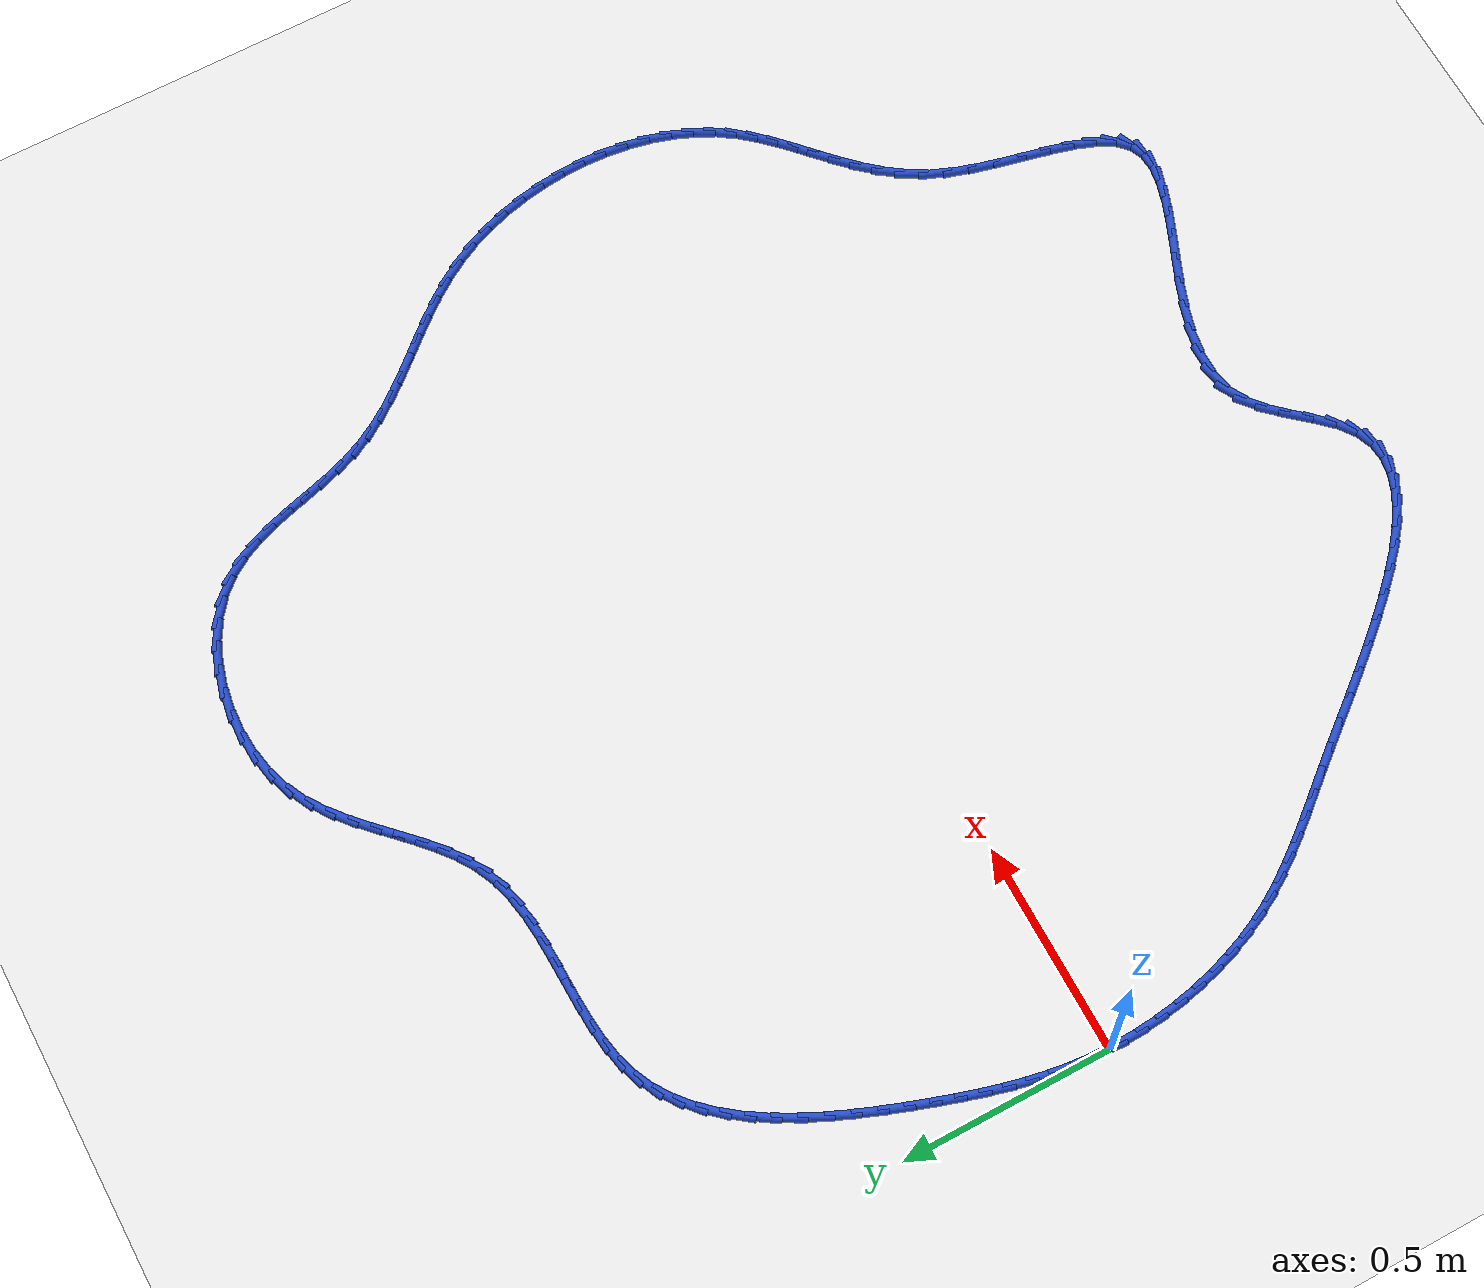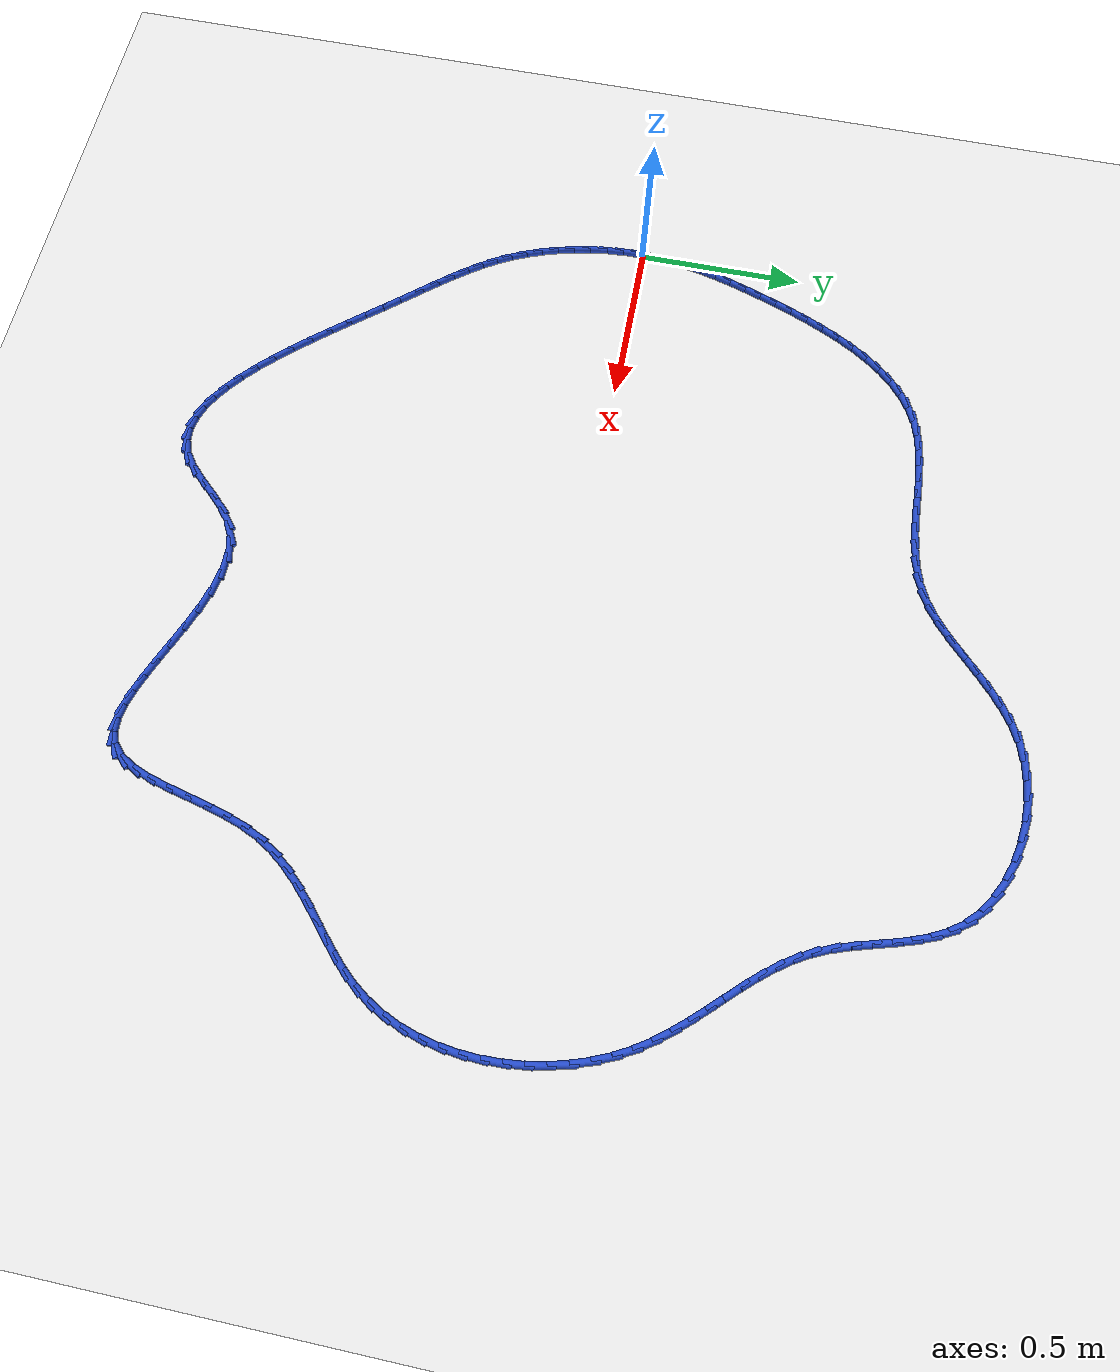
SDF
<sdf version="1.6">
 <world name="default">
  <light name="sun" type="directional">
   <pose>0 0 10 0 -0 0</pose>
   <diffuse>0.8 0.8 0.8 1</diffuse>
   <specular>0.2 0.2 0.2 1</specular>
   <attenuation>
    <range>1000</range>
    <constant>0.9</constant>
    <linear>0.01</linear>
    <quadratic>0.001</quadratic>
   </attenuation>
   <direction>-0.5 0.1 -0.9</direction>
  </light>
  <model name="ground_plane">
   <static>1</static>
   <link name="link">
    <collision name="collision">
     <geometry><plane><normal>0 0 1</normal><size>100 100</size></plane></geometry>
     <surface><friction><ode><mu>100</mu><mu2>50</mu2></ode></friction></surface>
    </collision>
    <visual name="visual">
     <cast_shadows>0</cast_shadows>
     <geometry><plane><normal>0 0 1</normal><size>100 100</size></plane></geometry>
     <material>
      <script><uri>file://media/materials/scripts/gazebo.material</uri><name>Gazebo/WhiteGlow</name></script>
     </material>
    </visual>
   </link>
  </model>
  <gravity>0 0 -9.8</gravity>
  <magnetic_field>6e-06 2.3e-05 -4.2e-05</magnetic_field>
  <atmosphere type="adiabatic"/>
  <physics name="default_physics" default="0" type="ode">
   <max_step_size>0.001</max_step_size>
   <real_time_factor>1</real_time_factor>
   <real_time_update_rate>1000</real_time_update_rate>
  </physics>
  <scene><ambient>0.4 0.4 0.4 1</ambient><background>0.7 0.7 0.7 1</background><shadows>1</shadows></scene>
  <spherical_coordinates>
   <surface_model>EARTH_WGS84</surface_model>
   <latitude_deg>0</latitude_deg>
   <longitude_deg>0</longitude_deg>
   <elevation>0</elevation>
   <heading_deg>0</heading_deg>
  </spherical_coordinates>
  <model name="line">
   <link name="link_0">
    <pose>-6.938893903907228e-18 1.3877787807814457e-17 0.01 0 1.57 1.52378141872039</pose>
    <collision name="collision">
     <geometry><cylinder><radius>0.01</radius><length>0.08</length></cylinder></geometry>
    </collision>
    <visual name="visual">
     <material>
      <script><name>Gazebo/Blue</name><uri>file://media/materials/scripts/gazebo.material</uri></script>
     </material>
     <geometry><cylinder><radius>0.01</radius><length>0.08</length></cylinder></geometry>
    </visual>
   </link>
   <link name="link_1">
    <pose>0.0024110733575314065 0.051245375440386036 0.01 0 1.57 1.466990602623562</pose>
    <collision name="collision">
     <geometry><cylinder><radius>0.01</radius><length>0.08</length></cylinder></geometry>
    </collision>
    <visual name="visual">
     <material>
      <script><name>Gazebo/Blue</name><uri>file://media/materials/scripts/gazebo.material</uri></script>
     </material>
     <geometry><cylinder><radius>0.01</radius><length>0.08</length></cylinder></geometry>
    </visual>
   </link>
   <link name="link_2">
    <pose>0.00768037519130564 0.10182410398176842 0.01 0 1.57 1.4148712306477755</pose>
    <collision name="collision">
     <geometry><cylinder><radius>0.01</radius><length>0.08</length></cylinder></geometry>
    </collision>
    <visual name="visual">
     <material>
      <script><name>Gazebo/Blue</name><uri>file://media/materials/scripts/gazebo.material</uri></script>
     </material>
     <geometry><cylinder><radius>0.01</radius><length>0.08</length></cylinder></geometry>
    </visual>
   </link>
   <link name="link_3">
    <pose>0.015563070977900464 0.15196811003572114 0.01 0 1.57 1.3683420249566505</pose>
    <collision name="collision">
     <geometry><cylinder><radius>0.01</radius><length>0.08</length></cylinder></geometry>
    </collision>
    <visual name="visual">
     <material>
      <script><name>Gazebo/Blue</name><uri>file://media/materials/scripts/gazebo.material</uri></script>
     </material>
     <geometry><cylinder><radius>0.01</radius><length>0.08</length></cylinder></geometry>
    </visual>
   </link>
   <link name="link_4">
    <pose>0.025814326193893615 0.2019093180138182 0.01 0 1.57 1.3280339136320554</pose>
    <collision name="collision">
     <geometry><cylinder><radius>0.01</radius><length>0.08</length></cylinder></geometry>
    </collision>
    <visual name="visual">
     <material>
      <script><name>Gazebo/Blue</name><uri>file://media/materials/scripts/gazebo.material</uri></script>
     </material>
     <geometry><cylinder><radius>0.01</radius><length>0.08</length></cylinder></geometry>
    </visual>
   </link>
   <link name="link_5">
    <pose>0.038189306315862856 0.25187965232763354 0.01 0 1.57 1.2943004729907877</pose>
    <collision name="collision">
     <geometry><cylinder><radius>0.01</radius><length>0.08</length></cylinder></geometry>
    </collision>
    <visual name="visual">
     <material>
      <script><name>Gazebo/Blue</name><uri>file://media/materials/scripts/gazebo.material</uri></script>
     </material>
     <geometry><cylinder><radius>0.01</radius><length>0.08</length></cylinder></geometry>
    </visual>
   </link>
   <link name="link_6">
    <pose>0.052443176820385955 0.3021110373887412 0.01 0 1.57 1.2672548912655726</pose>
    <collision name="collision">
     <geometry><cylinder><radius>0.01</radius><length>0.08</length></cylinder></geometry>
    </collision>
    <visual name="visual">
     <material>
      <script><name>Gazebo/Blue</name><uri>file://media/materials/scripts/gazebo.material</uri></script>
     </material>
     <geometry><cylinder><radius>0.01</radius><length>0.08</length></cylinder></geometry>
    </visual>
   </link>
   <link name="link_7">
    <pose>0.06833110318404062 0.3528353976087151 0.01 0 1.57 1.246818924104881</pose>
    <collision name="collision">
     <geometry><cylinder><radius>0.01</radius><length>0.08</length></cylinder></geometry>
    </collision>
    <visual name="visual">
     <material>
      <script><name>Gazebo/Blue</name><uri>file://media/materials/scripts/gazebo.material</uri></script>
     </material>
     <geometry><cylinder><radius>0.01</radius><length>0.08</length></cylinder></geometry>
    </visual>
   </link>
   <link name="link_8">
    <pose>0.08560825088340465 0.4042846573991291 0.01 0 1.57 1.2309105991806633</pose>
    <collision name="collision">
     <geometry><cylinder><radius>0.01</radius><length>0.08</length></cylinder></geometry>
    </collision>
    <visual name="visual">
     <material>
      <script><name>Gazebo/Blue</name><uri>file://media/materials/scripts/gazebo.material</uri></script>
     </material>
     <geometry><cylinder><radius>0.01</radius><length>0.08</length></cylinder></geometry>
    </visual>
   </link>
   <link name="link_9">
    <pose>0.10409419483523223 0.45656268177239095 0.01 0 1.57 1.2107166617826481</pose>
    <collision name="collision">
     <geometry><cylinder><radius>0.01</radius><length>0.08</length></cylinder></geometry>
    </collision>
    <visual name="visual">
     <material>
      <script><name>Gazebo/Blue</name><uri>file://media/materials/scripts/gazebo.material</uri></script>
     </material>
     <geometry><cylinder><radius>0.01</radius><length>0.08</length></cylinder></geometry>
    </visual>
   </link>
   <link name="link_10">
    <pose>0.12390542286041203 0.5091830109685765 0.01 0 1.57 1.1834522085738843</pose>
    <collision name="collision">
     <geometry><cylinder><radius>0.01</radius><length>0.08</length></cylinder></geometry>
    </collision>
    <visual name="visual">
     <material>
      <script><name>Gazebo/Blue</name><uri>file://media/materials/scripts/gazebo.material</uri></script>
     </material>
     <geometry><cylinder><radius>0.01</radius><length>0.08</length></cylinder></geometry>
    </visual>
   </link>
   <link name="link_11">
    <pose>0.14524392196312547 0.5614891950211758 0.01 0 1.57 1.1484810443017155</pose>
    <collision name="collision">
     <geometry><cylinder><radius>0.01</radius><length>0.08</length></cylinder></geometry>
    </collision>
    <visual name="visual">
     <material>
      <script><name>Gazebo/Blue</name><uri>file://media/materials/scripts/gazebo.material</uri></script>
     </material>
     <geometry><cylinder><radius>0.01</radius><length>0.08</length></cylinder></geometry>
    </visual>
   </link>
   <link name="link_12">
    <pose>0.1683116869953638 0.6128247683605962 0.01 0 1.57 1.1048214126106137</pose>
    <collision name="collision">
     <geometry><cylinder><radius>0.01</radius><length>0.08</length></cylinder></geometry>
    </collision>
    <visual name="visual">
     <material>
      <script><name>Gazebo/Blue</name><uri>file://media/materials/scripts/gazebo.material</uri></script>
     </material>
     <geometry><cylinder><radius>0.01</radius><length>0.08</length></cylinder></geometry>
    </visual>
   </link>
   <link name="link_13">
    <pose>0.19331071280911832 0.662533265417245 0.01 0 1.57 1.0511368247239044</pose>
    <collision name="collision">
     <geometry><cylinder><radius>0.01</radius><length>0.08</length></cylinder></geometry>
    </collision>
    <visual name="visual">
     <material>
      <script><name>Gazebo/Blue</name><uri>file://media/materials/scripts/gazebo.material</uri></script>
     </material>
     <geometry><cylinder><radius>0.01</radius><length>0.08</length></cylinder></geometry>
    </visual>
   </link>
   <link name="link_14">
    <pose>0.22044299425638023 0.7099582206215298 0.01 0 1.57 0.9857424128663043</pose>
    <collision name="collision">
     <geometry><cylinder><radius>0.01</radius><length>0.08</length></cylinder></geometry>
    </collision>
    <visual name="visual">
     <material>
      <script><name>Gazebo/Blue</name><uri>file://media/materials/scripts/gazebo.material</uri></script>
     </material>
     <geometry><cylinder><radius>0.01</radius><length>0.08</length></cylinder></geometry>
    </visual>
   </link>
   <link name="link_15">
    <pose>0.24991052618914075 0.7544431684038578 0.01 0 1.57 0.9066727954461855</pose>
    <collision name="collision">
     <geometry><cylinder><radius>0.01</radius><length>0.08</length></cylinder></geometry>
    </collision>
    <visual name="visual">
     <material>
      <script><name>Gazebo/Blue</name><uri>file://media/materials/scripts/gazebo.material</uri></script>
     </material>
     <geometry><cylinder><radius>0.01</radius><length>0.08</length></cylinder></geometry>
    </visual>
   </link>
   <link name="link_16">
    <pose>0.28191530345939125 0.7953316431946366 0.01 0 1.57 0.811891411169998</pose>
    <collision name="collision">
     <geometry><cylinder><radius>0.01</radius><length>0.08</length></cylinder></geometry>
    </collision>
    <visual name="visual">
     <material>
      <script><name>Gazebo/Blue</name><uri>file://media/materials/scripts/gazebo.material</uri></script>
     </material>
     <geometry><cylinder><radius>0.01</radius><length>0.08</length></cylinder></geometry>
    </visual>
   </link>
   <link name="link_17">
    <pose>0.31665932091912274 0.8319671794242733 0.01 0 1.57 0.6997559581888386</pose>
    <collision name="collision">
     <geometry><cylinder><radius>0.01</radius><length>0.08</length></cylinder></geometry>
    </collision>
    <visual name="visual">
     <material>
      <script><name>Gazebo/Blue</name><uri>file://media/materials/scripts/gazebo.material</uri></script>
     </material>
     <geometry><cylinder><radius>0.01</radius><length>0.08</length></cylinder></geometry>
    </visual>
   </link>
   <link name="link_18">
    <pose>0.3543445734203267 0.8636933115231757 0.01 0 1.57 0.5698348710611841</pose>
    <collision name="collision">
     <geometry><cylinder><radius>0.01</radius><length>0.08</length></cylinder></geometry>
    </collision>
    <visual name="visual">
     <material>
      <script><name>Gazebo/Blue</name><uri>file://media/materials/scripts/gazebo.material</uri></script>
     </material>
     <geometry><cylinder><radius>0.01</radius><length>0.08</length></cylinder></geometry>
    </visual>
   </link>
   <link name="link_19">
    <pose>0.3951730558149943 0.8898535739217508 0.01 0 1.57 0.42413232272207957</pose>
    <collision name="collision">
     <geometry><cylinder><radius>0.01</radius><length>0.08</length></cylinder></geometry>
    </collision>
    <visual name="visual">
     <material>
      <script><name>Gazebo/Blue</name><uri>file://media/materials/scripts/gazebo.material</uri></script>
     </material>
     <geometry><cylinder><radius>0.01</radius><length>0.08</length></cylinder></geometry>
    </visual>
   </link>
   <link name="link_20">
    <pose>0.4393437593304431 0.9097983320072475 0.01 0 1.57 0.2817256883511118</pose>
    <collision name="collision">
     <geometry><cylinder><radius>0.01</radius><length>0.08</length></cylinder></geometry>
    </collision>
    <visual name="visual">
     <material>
      <script><name>Gazebo/Blue</name><uri>file://media/materials/scripts/gazebo.material</uri></script>
     </material>
     <geometry><cylinder><radius>0.01</radius><length>0.08</length></cylinder></geometry>
    </visual>
   </link>
   <link name="link_21">
    <pose>0.4867711848116862 0.9235249499548267 0.01 0 1.57 0.17152300022071781</pose>
    <collision name="collision">
     <geometry><cylinder><radius>0.01</radius><length>0.08</length></cylinder></geometry>
    </collision>
    <visual name="visual">
     <material>
      <script><name>Gazebo/Blue</name><uri>file://media/materials/scripts/gazebo.material</uri></script>
     </material>
     <geometry><cylinder><radius>0.01</radius><length>0.08</length></cylinder></geometry>
    </visual>
   </link>
   <link name="link_22">
    <pose>0.5368553760978376 0.9322007895211278 0.01 0 1.57 0.09409261308504</pose>
    <collision name="collision">
     <geometry><cylinder><radius>0.01</radius><length>0.08</length></cylinder></geometry>
    </collision>
    <visual name="visual">
     <material>
      <script><name>Gazebo/Blue</name><uri>file://media/materials/scripts/gazebo.material</uri></script>
     </material>
     <geometry><cylinder><radius>0.01</radius><length>0.08</length></cylinder></geometry>
    </visual>
   </link>
   <link name="link_23">
    <pose>0.5889422566244674 0.9371162951315637 0.01 0 1.57 0.04573571768627673</pose>
    <collision name="collision">
     <geometry><cylinder><radius>0.01</radius><length>0.08</length></cylinder></geometry>
    </collision>
    <visual name="visual">
     <material>
      <script><name>Gazebo/Blue</name><uri>file://media/materials/scripts/gazebo.material</uri></script>
     </material>
     <geometry><cylinder><radius>0.01</radius><length>0.08</length></cylinder></geometry>
    </visual>
   </link>
   <link name="link_24">
    <pose>0.642377749827145 0.9395619112115469 0.01 0 1.57 0.023387020796661953</pose>
    <collision name="collision">
     <geometry><cylinder><radius>0.01</radius><length>0.08</length></cylinder></geometry>
    </collision>
    <visual name="visual">
     <material>
      <script><name>Gazebo/Blue</name><uri>file://media/materials/scripts/gazebo.material</uri></script>
     </material>
     <geometry><cylinder><radius>0.01</radius><length>0.08</length></cylinder></geometry>
    </visual>
   </link>
   <link name="link_25">
    <pose>0.6965077791414405 0.9408280821864908 0.01 0 1.57 0.02541741343297647</pose>
    <collision name="collision">
     <geometry><cylinder><radius>0.01</radius><length>0.08</length></cylinder></geometry>
    </collision>
    <visual name="visual">
     <material>
      <script><name>Gazebo/Blue</name><uri>file://media/materials/scripts/gazebo.material</uri></script>
     </material>
     <geometry><cylinder><radius>0.01</radius><length>0.08</length></cylinder></geometry>
    </visual>
   </link>
   <link name="link_26">
    <pose>0.7506782680029233 0.9422052524818081 0.01 0 1.57 0.051835084882170944</pose>
    <collision name="collision">
     <geometry><cylinder><radius>0.01</radius><length>0.08</length></cylinder></geometry>
    </collision>
    <visual name="visual">
     <material>
      <script><name>Gazebo/Blue</name><uri>file://media/materials/scripts/gazebo.material</uri></script>
     </material>
     <geometry><cylinder><radius>0.01</radius><length>0.08</length></cylinder></geometry>
    </visual>
   </link>
   <link name="link_27">
    <pose>0.804235139847164 0.9449838665229118 0.01 0 1.57 0.10424094520519987</pose>
    <collision name="collision">
     <geometry><cylinder><radius>0.01</radius><length>0.08</length></cylinder></geometry>
    </collision>
    <visual name="visual">
     <material>
      <script><name>Gazebo/Blue</name><uri>file://media/materials/scripts/gazebo.material</uri></script>
     </material>
     <geometry><cylinder><radius>0.01</radius><length>0.08</length></cylinder></geometry>
    </visual>
   </link>
   <link name="link_28">
    <pose>0.8565243181097312 0.9504543687352144 0.01 0 1.57 0.18551952304503483</pose>
    <collision name="collision">
     <geometry><cylinder><radius>0.01</radius><length>0.08</length></cylinder></geometry>
    </collision>
    <visual name="visual">
     <material>
      <script><name>Gazebo/Blue</name><uri>file://media/materials/scripts/gazebo.material</uri></script>
     </material>
     <geometry><cylinder><radius>0.01</radius><length>0.08</length></cylinder></geometry>
    </visual>
   </link>
   <link name="link_29">
    <pose>0.9068917262261957 0.9599072035441296 0.01 0 1.57 0.2988910383332058</pose>
    <collision name="collision">
     <geometry><cylinder><radius>0.01</radius><length>0.08</length></cylinder></geometry>
    </collision>
    <visual name="visual">
     <material>
      <script><name>Gazebo/Blue</name><uri>file://media/materials/scripts/gazebo.material</uri></script>
     </material>
     <geometry><cylinder><radius>0.01</radius><length>0.08</length></cylinder></geometry>
    </visual>
   </link>
   <link name="link_30">
    <pose>0.9546832876321268 0.9746328153750697 0.01 0 1.57 0.44314500986465155</pose>
    <collision name="collision">
     <geometry><cylinder><radius>0.01</radius><length>0.08</length></cylinder></geometry>
    </collision>
    <visual name="visual">
     <material>
      <script><name>Gazebo/Blue</name><uri>file://media/materials/scripts/gazebo.material</uri></script>
     </material>
     <geometry><cylinder><radius>0.01</radius><length>0.08</length></cylinder></geometry>
    </visual>
   </link>
   <link name="link_31">
    <pose>0.9993039648195952 0.9958110510397098 0.01 0 1.57 0.579689639556957</pose>
    <collision name="collision">
     <geometry><cylinder><radius>0.01</radius><length>0.08</length></cylinder></geometry>
    </collision>
    <visual name="visual">
     <material>
      <script><name>Gazebo/Blue</name><uri>file://media/materials/scripts/gazebo.material</uri></script>
     </material>
     <geometry><cylinder><radius>0.01</radius><length>0.08</length></cylinder></geometry>
    </visual>
   </link>
   <link name="link_32">
    <pose>1.0409744091179232 1.0230937309160446 0.01 0 1.57 0.6792841769361144</pose>
    <collision name="collision">
     <geometry><cylinder><radius>0.01</radius><length>0.08</length></cylinder></geometry>
    </collision>
    <visual name="visual">
     <material>
      <script><name>Gazebo/Blue</name><uri>file://media/materials/scripts/gazebo.material</uri></script>
     </material>
     <geometry><cylinder><radius>0.01</radius><length>0.08</length></cylinder></geometry>
    </visual>
   </link>
   <link name="link_33">
    <pose>1.0805102676530278 1.0550180722839213 0.01 0 1.57 0.7424207594840871</pose>
    <collision name="collision">
     <geometry><cylinder><radius>0.01</radius><length>0.08</length></cylinder></geometry>
    </collision>
    <visual name="visual">
     <material>
      <script><name>Gazebo/Blue</name><uri>file://media/materials/scripts/gazebo.material</uri></script>
     </material>
     <geometry><cylinder><radius>0.01</radius><length>0.08</length></cylinder></geometry>
    </visual>
   </link>
   <link name="link_34">
    <pose>1.1187407062930197 1.0900959678208653 0.01 0 1.57 0.771830193548512</pose>
    <collision name="collision">
     <geometry><cylinder><radius>0.01</radius><length>0.08</length></cylinder></geometry>
    </collision>
    <visual name="visual">
     <material>
      <script><name>Gazebo/Blue</name><uri>file://media/materials/scripts/gazebo.material</uri></script>
     </material>
     <geometry><cylinder><radius>0.01</radius><length>0.08</length></cylinder></geometry>
    </visual>
   </link>
   <link name="link_35">
    <pose>1.156494890906009 1.126839310204401 0.01 0 1.57 0.7695864773913116</pose>
    <collision name="collision">
     <geometry><cylinder><radius>0.01</radius><length>0.08</length></cylinder></geometry>
    </collision>
    <visual name="visual">
     <material>
      <script><name>Gazebo/Blue</name><uri>file://media/materials/scripts/gazebo.material</uri></script>
     </material>
     <geometry><cylinder><radius>0.01</radius><length>0.08</length></cylinder></geometry>
    </visual>
   </link>
   <link name="link_36">
    <pose>1.1946019873601066 1.1637599921120545 0.01 0 1.57 0.7363147233643089</pose>
    <collision name="collision">
     <geometry><cylinder><radius>0.01</radius><length>0.08</length></cylinder></geometry>
    </collision>
    <visual name="visual">
     <material>
      <script><name>Gazebo/Blue</name><uri>file://media/materials/scripts/gazebo.material</uri></script>
     </material>
     <geometry><cylinder><radius>0.01</radius><length>0.08</length></cylinder></geometry>
    </visual>
   </link>
   <link name="link_37">
    <pose>1.2338911615234232 1.1993699062213505 0.01 0 1.57 0.6713464659414836</pose>
    <collision name="collision">
     <geometry><cylinder><radius>0.01</radius><length>0.08</length></cylinder></geometry>
    </collision>
    <visual name="visual">
     <material>
      <script><name>Gazebo/Blue</name><uri>file://media/materials/scripts/gazebo.material</uri></script>
     </material>
     <geometry><cylinder><radius>0.01</radius><length>0.08</length></cylinder></geometry>
    </visual>
   </link>
   <link name="link_38">
    <pose>1.2751915792640687 1.2321809452098147 0.01 0 1.57 0.5737032867098244</pose>
    <collision name="collision">
     <geometry><cylinder><radius>0.01</radius><length>0.08</length></cylinder></geometry>
    </collision>
    <visual name="visual">
     <material>
      <script><name>Gazebo/Blue</name><uri>file://media/materials/scripts/gazebo.material</uri></script>
     </material>
     <geometry><cylinder><radius>0.01</radius><length>0.08</length></cylinder></geometry>
    </visual>
   </link>
   <link name="link_39">
    <pose>1.319332406450154 1.2607050017549721 0.01 0 1.57 0.44420014987154566</pose>
    <collision name="collision">
     <geometry><cylinder><radius>0.01</radius><length>0.08</length></cylinder></geometry>
    </collision>
    <visual name="visual">
     <material>
      <script><name>Gazebo/Blue</name><uri>file://media/materials/scripts/gazebo.material</uri></script>
     </material>
     <geometry><cylinder><radius>0.01</radius><length>0.08</length></cylinder></geometry>
    </visual>
   </link>
   <link name="link_40">
    <pose>1.3671389212579728 1.2834571629338003 0.01 0 1.57 0.30009435325279094</pose>
    <collision name="collision">
     <geometry><cylinder><radius>0.01</radius><length>0.08</length></cylinder></geometry>
    </collision>
    <visual name="visual">
     <material>
      <script><name>Gazebo/Blue</name><uri>file://media/materials/scripts/gazebo.material</uri></script>
     </material>
     <geometry><cylinder><radius>0.01</radius><length>0.08</length></cylinder></geometry>
    </visual>
   </link>
   <link name="link_41">
    <pose>1.4188285382098815 1.2994519791077745 0.01 0 1.57 0.16874691366268352</pose>
    <collision name="collision">
     <geometry><cylinder><radius>0.01</radius><length>0.08</length></cylinder></geometry>
    </collision>
    <visual name="visual">
     <material>
      <script><name>Gazebo/Blue</name><uri>file://media/materials/scripts/gazebo.material</uri></script>
     </material>
     <geometry><cylinder><radius>0.01</radius><length>0.08</length></cylinder></geometry>
    </visual>
   </link>
   <link name="link_42">
    <pose>1.4733558347454327 1.308741635892709 0.01 0 1.57 0.049208795846518584</pose>
    <collision name="collision">
     <geometry><cylinder><radius>0.01</radius><length>0.08</length></cylinder></geometry>
    </collision>
    <visual name="visual">
     <material>
      <script><name>Gazebo/Blue</name><uri>file://media/materials/scripts/gazebo.material</uri></script>
     </material>
     <geometry><cylinder><radius>0.01</radius><length>0.08</length></cylinder></geometry>
    </visual>
   </link>
   <link name="link_43">
    <pose>1.5295181134567455 1.3115075469169166 0.01 0 1.57 -0.06310980268239884</pose>
    <collision name="collision">
     <geometry><cylinder><radius>0.01</radius><length>0.08</length></cylinder></geometry>
    </collision>
    <visual name="visual">
     <material>
      <script><name>Gazebo/Blue</name><uri>file://media/materials/scripts/gazebo.material</uri></script>
     </material>
     <geometry><cylinder><radius>0.01</radius><length>0.08</length></cylinder></geometry>
    </visual>
   </link>
   <link name="link_44">
    <pose>1.586112676935939 1.30793112580871 0.01 0 1.57 -0.17269138543104987</pose>
    <collision name="collision">
     <geometry><cylinder><radius>0.01</radius><length>0.08</length></cylinder></geometry>
    </collision>
    <visual name="visual">
     <material>
      <script><name>Gazebo/Blue</name><uri>file://media/materials/scripts/gazebo.material</uri></script>
     </material>
     <geometry><cylinder><radius>0.01</radius><length>0.08</length></cylinder></geometry>
    </visual>
   </link>
   <link name="link_45">
    <pose>1.641936827775133 1.2981937861964032 0.01 0 1.57 -0.28397021775024467</pose>
    <collision name="collision">
     <geometry><cylinder><radius>0.01</radius><length>0.08</length></cylinder></geometry>
    </collision>
    <visual name="visual">
     <material>
      <script><name>Gazebo/Blue</name><uri>file://media/materials/scripts/gazebo.material</uri></script>
     </material>
     <geometry><cylinder><radius>0.01</radius><length>0.08</length></cylinder></geometry>
    </visual>
   </link>
   <link name="link_46">
    <pose>1.6957878685664447 1.282476941708308 0.01 0 1.57 -0.4015022293594167</pose>
    <collision name="collision">
     <geometry><cylinder><radius>0.01</radius><length>0.08</length></cylinder></geometry>
    </collision>
    <visual name="visual">
     <material>
      <script><name>Gazebo/Blue</name><uri>file://media/materials/scripts/gazebo.material</uri></script>
     </material>
     <geometry><cylinder><radius>0.01</radius><length>0.08</length></cylinder></geometry>
    </visual>
   </link>
   <link name="link_47">
    <pose>1.7464631019019936 1.2609620059727369 0.01 0 1.57 -0.5300895994952739</pose>
    <collision name="collision">
     <geometry><cylinder><radius>0.01</radius><length>0.08</length></cylinder></geometry>
    </collision>
    <visual name="visual">
     <material>
      <script><name>Gazebo/Blue</name><uri>file://media/materials/scripts/gazebo.material</uri></script>
     </material>
     <geometry><cylinder><radius>0.01</radius><length>0.08</length></cylinder></geometry>
    </visual>
   </link>
   <link name="link_48">
    <pose>1.792759830373899 1.2338303926180039 0.01 0 1.57 -0.6746579154839316</pose>
    <collision name="collision">
     <geometry><cylinder><radius>0.01</radius><length>0.08</length></cylinder></geometry>
    </collision>
    <visual name="visual">
     <material>
      <script><name>Gazebo/Blue</name><uri>file://media/materials/scripts/gazebo.material</uri></script>
     </material>
     <geometry><cylinder><radius>0.01</radius><length>0.08</length></cylinder></geometry>
    </visual>
   </link>
   <link name="link_49">
    <pose>1.8334753565742794 1.2012635152724211 0.01 0 1.57 -0.8392508939017052</pose>
    <collision name="collision">
     <geometry><cylinder><radius>0.01</radius><length>0.08</length></cylinder></geometry>
    </collision>
    <visual name="visual">
     <material>
      <script><name>Gazebo/Blue</name><uri>file://media/materials/scripts/gazebo.material</uri></script>
     </material>
     <geometry><cylinder><radius>0.01</radius><length>0.08</length></cylinder></geometry>
    </visual>
   </link>
   <link name="link_50">
    <pose>1.8674227503506156 1.163447738502064 0.01 0 1.57 -1.0054576230856267</pose>
    <collision name="collision">
     <geometry><cylinder><radius>0.01</radius><length>0.08</length></cylinder></geometry>
    </collision>
    <visual name="visual">
     <material>
      <script><name>Gazebo/Blue</name><uri>file://media/materials/scripts/gazebo.material</uri></script>
     </material>
     <geometry><cylinder><radius>0.01</radius><length>0.08</length></cylinder></geometry>
    </visual>
   </link>
   <link name="link_51">
    <pose>1.8944242270578622 1.1208862998154685 0.01 0 1.57 -1.1364373690017735</pose>
    <collision name="collision">
     <geometry><cylinder><radius>0.01</radius><length>0.08</length></cylinder></geometry>
    </collision>
    <visual name="visual">
     <material>
      <script><name>Gazebo/Blue</name><uri>file://media/materials/scripts/gazebo.material</uri></script>
     </material>
     <geometry><cylinder><radius>0.01</radius><length>0.08</length></cylinder></geometry>
    </visual>
   </link>
   <link name="link_52">
    <pose>1.9159035873387094 1.0745853364902984 0.01 0 1.57 -1.227284310028582</pose>
    <collision name="collision">
     <geometry><cylinder><radius>0.01</radius><length>0.08</length></cylinder></geometry>
    </collision>
    <visual name="visual">
     <material>
      <script><name>Gazebo/Blue</name><uri>file://media/materials/scripts/gazebo.material</uri></script>
     </material>
     <geometry><cylinder><radius>0.01</radius><length>0.08</length></cylinder></geometry>
    </visual>
   </link>
   <link name="link_53">
    <pose>1.9334268696665902 1.0255956486596944 0.01 0 1.57 -1.2803372340325765</pose>
    <collision name="collision">
     <geometry><cylinder><radius>0.01</radius><length>0.08</length></cylinder></geometry>
    </collision>
    <visual name="visual">
     <material>
      <script><name>Gazebo/Blue</name><uri>file://media/materials/scripts/gazebo.material</uri></script>
     </material>
     <geometry><cylinder><radius>0.01</radius><length>0.08</length></cylinder></geometry>
    </visual>
   </link>
   <link name="link_54">
    <pose>1.9485601125149417 0.9749680364567993 0.01 0 1.57 -1.298346906897571</pose>
    <collision name="collision">
     <geometry><cylinder><radius>0.01</radius><length>0.08</length></cylinder></geometry>
    </collision>
    <visual name="visual">
     <material>
      <script><name>Gazebo/Blue</name><uri>file://media/materials/scripts/gazebo.material</uri></script>
     </material>
     <geometry><cylinder><radius>0.01</radius><length>0.08</length></cylinder></geometry>
    </visual>
   </link>
   <link name="link_55">
    <pose>1.9628693543571967 0.9237533000147554 0.01 0 1.57 -1.2824886091502063</pose>
    <collision name="collision">
     <geometry><cylinder><radius>0.01</radius><length>0.08</length></cylinder></geometry>
    </collision>
    <visual name="visual">
     <material>
      <script><name>Gazebo/Blue</name><uri>file://media/materials/scripts/gazebo.material</uri></script>
     </material>
     <geometry><cylinder><radius>0.01</radius><length>0.08</length></cylinder></geometry>
    </visual>
   </link>
   <link name="link_56">
    <pose>1.9779206336667894 0.8730022394667043 0.01 0 1.57 -1.2318335838799885</pose>
    <collision name="collision">
     <geometry><cylinder><radius>0.01</radius><length>0.08</length></cylinder></geometry>
    </collision>
    <visual name="visual">
     <material>
      <script><name>Gazebo/Blue</name><uri>file://media/materials/scripts/gazebo.material</uri></script>
     </material>
     <geometry><cylinder><radius>0.01</radius><length>0.08</length></cylinder></geometry>
    </visual>
   </link>
   <link name="link_57">
    <pose>1.9952799889171555 0.8237656549457882 0.01 0 1.57 -1.1446937407474338</pose>
    <collision name="collision">
     <geometry><cylinder><radius>0.01</radius><length>0.08</length></cylinder></geometry>
    </collision>
    <visual name="visual">
     <material>
      <script><name>Gazebo/Blue</name><uri>file://media/materials/scripts/gazebo.material</uri></script>
     </material>
     <geometry><cylinder><radius>0.01</radius><length>0.08</length></cylinder></geometry>
    </visual>
   </link>
   <link name="link_58">
    <pose>2.0164763853886774 0.7770685309317367 0.01 0 1.57 -1.0445885596585376</pose>
    <collision name="collision">
     <geometry><cylinder><radius>0.01</radius><length>0.08</length></cylinder></geometry>
    </collision>
    <visual name="visual">
     <material>
      <script><name>Gazebo/Blue</name><uri>file://media/materials/scripts/gazebo.material</uri></script>
     </material>
     <geometry><cylinder><radius>0.01</radius><length>0.08</length></cylinder></geometry>
    </visual>
   </link>
   <link name="link_59">
    <pose>2.041964020131025 0.7331874447168143 0.01 0 1.57 -0.9621029545298629</pose>
    <collision name="collision">
     <geometry><cylinder><radius>0.01</radius><length>0.08</length></cylinder></geometry>
    </collision>
    <visual name="visual">
     <material>
      <script><name>Gazebo/Blue</name><uri>file://media/materials/scripts/gazebo.material</uri></script>
     </material>
     <geometry><cylinder><radius>0.01</radius><length>0.08</length></cylinder></geometry>
    </visual>
   </link>
   <link name="link_60">
    <pose>2.070982215114004 0.6915530040012731 0.01 0 1.57 -0.9003262605472824</pose>
    <collision name="collision">
     <geometry><cylinder><radius>0.01</radius><length>0.08</length></cylinder></geometry>
    </collision>
    <visual name="visual">
     <material>
      <script><name>Gazebo/Blue</name><uri>file://media/materials/scripts/gazebo.material</uri></script>
     </material>
     <geometry><cylinder><radius>0.01</radius><length>0.08</length></cylinder></geometry>
    </visual>
   </link>
   <link name="link_61">
    <pose>2.102705065784034 0.6515503964612879 0.01 0 1.57 -0.8594352487268361</pose>
    <collision name="collision">
     <geometry><cylinder><radius>0.01</radius><length>0.08</length></cylinder></geometry>
    </collision>
    <visual name="visual">
     <material>
      <script><name>Gazebo/Blue</name><uri>file://media/materials/scripts/gazebo.material</uri></script>
     </material>
     <geometry><cylinder><radius>0.01</radius><length>0.08</length></cylinder></geometry>
    </visual>
   </link>
   <link name="link_62">
    <pose>2.1363066675875353 0.612564809773034 0.01 0 1.57 -0.8389929711335402</pose>
    <collision name="collision">
     <geometry><cylinder><radius>0.01</radius><length>0.08</length></cylinder></geometry>
    </collision>
    <visual name="visual">
     <material>
      <script><name>Gazebo/Blue</name><uri>file://media/materials/scripts/gazebo.material</uri></script>
     </material>
     <geometry><cylinder><radius>0.01</radius><length>0.08</length></cylinder></geometry>
    </visual>
   </link>
   <link name="link_63">
    <pose>2.1709611159709272 0.5739814316126878 0.01 0 1.57 -0.838479782214066</pose>
    <collision name="collision">
     <geometry><cylinder><radius>0.01</radius><length>0.08</length></cylinder></geometry>
    </collision>
    <visual name="visual">
     <material>
      <script><name>Gazebo/Blue</name><uri>file://media/materials/scripts/gazebo.material</uri></script>
     </material>
     <geometry><cylinder><radius>0.01</radius><length>0.08</length></cylinder></geometry>
    </visual>
   </link>
   <link name="link_64">
    <pose>2.20584250638063 0.5351854496564243 0.01 0 1.57 -0.8575399914029248</pose>
    <collision name="collision">
     <geometry><cylinder><radius>0.01</radius><length>0.08</length></cylinder></geometry>
    </collision>
    <visual name="visual">
     <material>
      <script><name>Gazebo/Blue</name><uri>file://media/materials/scripts/gazebo.material</uri></script>
     </material>
     <geometry><cylinder><radius>0.01</radius><length>0.08</length></cylinder></geometry>
    </visual>
   </link>
   <link name="link_65">
    <pose>2.2401249342630627 0.4955620515804191 0.01 0 1.57 -0.8959802626697213</pose>
    <collision name="collision">
     <geometry><cylinder><radius>0.01</radius><length>0.08</length></cylinder></geometry>
    </collision>
    <visual name="visual">
     <material>
      <script><name>Gazebo/Blue</name><uri>file://media/materials/scripts/gazebo.material</uri></script>
     </material>
     <geometry><cylinder><radius>0.01</radius><length>0.08</length></cylinder></geometry>
    </visual>
   </link>
   <link name="link_66">
    <pose>2.272982495064645 0.4544964250608474 0.01 0 1.57 -0.9535493255962586</pose>
    <collision name="collision">
     <geometry><cylinder><radius>0.01</radius><length>0.08</length></cylinder></geometry>
    </collision>
    <visual name="visual">
     <material>
      <script><name>Gazebo/Blue</name><uri>file://media/materials/scripts/gazebo.material</uri></script>
     </material>
     <geometry><cylinder><radius>0.01</radius><length>0.08</length></cylinder></geometry>
    </visual>
   </link>
   <link name="link_67">
    <pose>2.303589284231798 0.4113737577738846 0.01 0 1.57 -1.0293351641206523</pose>
    <collision name="collision">
     <geometry><cylinder><radius>0.01</radius><length>0.08</length></cylinder></geometry>
    </collision>
    <visual name="visual">
     <material>
      <script><name>Gazebo/Blue</name><uri>file://media/materials/scripts/gazebo.material</uri></script>
     </material>
     <geometry><cylinder><radius>0.01</radius><length>0.08</length></cylinder></geometry>
    </visual>
   </link>
   <link name="link_68">
    <pose>2.331125530236421 0.36558818645795493 0.01 0 1.57 -1.1132000116904694</pose>
    <collision name="collision">
     <geometry><cylinder><radius>0.01</radius><length>0.08</length></cylinder></geometry>
    </collision>
    <visual name="visual">
     <material>
      <script><name>Gazebo/Blue</name><uri>file://media/materials/scripts/gazebo.material</uri></script>
     </material>
     <geometry><cylinder><radius>0.01</radius><length>0.08</length></cylinder></geometry>
    </visual>
   </link>
   <link name="link_69">
    <pose>2.3550689753679053 0.3169679679576361 0.01 0 1.57 -1.1928239296840712</pose>
    <collision name="collision">
     <geometry><cylinder><radius>0.01</radius><length>0.08</length></cylinder></geometry>
    </collision>
    <visual name="visual">
     <material>
      <script><name>Gazebo/Blue</name><uri>file://media/materials/scripts/gazebo.material</uri></script>
     </material>
     <geometry><cylinder><radius>0.01</radius><length>0.08</length></cylinder></geometry>
    </visual>
   </link>
   <link name="link_70">
    <pose>2.37532199601675 0.2659609679901375 0.01 0 1.57 -1.2684834164067018</pose>
    <collision name="collision">
     <geometry><cylinder><radius>0.01</radius><length>0.08</length></cylinder></geometry>
    </collision>
    <visual name="visual">
     <material>
      <script><name>Gazebo/Blue</name><uri>file://media/materials/scripts/gazebo.material</uri></script>
     </material>
     <geometry><cylinder><radius>0.01</radius><length>0.08</length></cylinder></geometry>
    </visual>
   </link>
   <link name="link_71">
    <pose>2.391819538722935 0.21306257731493594 0.01 0 1.57 -1.3414190692378956</pose>
    <collision name="collision">
     <geometry><cylinder><radius>0.01</radius><length>0.08</length></cylinder></geometry>
    </collision>
    <visual name="visual">
     <material>
      <script><name>Gazebo/Blue</name><uri>file://media/materials/scripts/gazebo.material</uri></script>
     </material>
     <geometry><cylinder><radius>0.01</radius><length>0.08</length></cylinder></geometry>
    </visual>
   </link>
   <link name="link_72">
    <pose>2.404496550026445 0.15876818669151 0.01 0 1.57 -1.4128437568094134</pose>
    <collision name="collision">
     <geometry><cylinder><radius>0.01</radius><length>0.08</length></cylinder></geometry>
    </collision>
    <visual name="visual">
     <material>
      <script><name>Gazebo/Blue</name><uri>file://media/materials/scripts/gazebo.material</uri></script>
     </material>
     <geometry><cylinder><radius>0.01</radius><length>0.08</length></cylinder></geometry>
    </visual>
   </link>
   <link name="link_73">
    <pose>2.4132879764672612 0.10357318687933671 0.01 0 1.57 -1.4839511261356757</pose>
    <collision name="collision">
     <geometry><cylinder><radius>0.01</radius><length>0.08</length></cylinder></geometry>
    </collision>
    <visual name="visual">
     <material>
      <script><name>Gazebo/Blue</name><uri>file://media/materials/scripts/gazebo.material</uri></script>
     </material>
     <geometry><cylinder><radius>0.01</radius><length>0.08</length></cylinder></geometry>
    </visual>
   </link>
   <link name="link_74">
    <pose>2.418128764585366 0.04797296863789368 0.01 0 1.57 -1.5559335111470167</pose>
    <collision name="collision">
     <geometry><cylinder><radius>0.01</radius><length>0.08</length></cylinder></geometry>
    </collision>
    <visual name="visual">
     <material>
      <script><name>Gazebo/Blue</name><uri>file://media/materials/scripts/gazebo.material</uri></script>
     </material>
     <geometry><cylinder><radius>0.01</radius><length>0.08</length></cylinder></geometry>
    </visual>
   </link>
   <link name="link_75">
    <pose>2.418953860920743 -0.00753707727334153 0.01 0 1.57 1.5115905988101848</pose>
    <collision name="collision">
     <geometry><cylinder><radius>0.01</radius><length>0.08</length></cylinder></geometry>
    </collision>
    <visual name="visual">
     <material>
      <script><name>Gazebo/Blue</name><uri>file://media/materials/scripts/gazebo.material</uri></script>
     </material>
     <geometry><cylinder><radius>0.01</radius><length>0.08</length></cylinder></geometry>
    </visual>
   </link>
   <link name="link_76">
    <pose>2.4156982120133725 -0.06246156009489186 0.01 0 1.57 1.4341903057175442</pose>
    <collision name="collision">
     <geometry><cylinder><radius>0.01</radius><length>0.08</length></cylinder></geometry>
    </collision>
    <visual name="visual">
     <material>
      <script><name>Gazebo/Blue</name><uri>file://media/materials/scripts/gazebo.material</uri></script>
     </material>
     <geometry><cylinder><radius>0.01</radius><length>0.08</length></cylinder></geometry>
    </visual>
   </link>
   <link name="link_77">
    <pose>2.408296764403238 -0.11630508906727932 0.01 0 1.57 1.352175333449702</pose>
    <collision name="collision">
     <geometry><cylinder><radius>0.01</radius><length>0.08</length></cylinder></geometry>
    </collision>
    <visual name="visual">
     <material>
      <script><name>Gazebo/Blue</name><uri>file://media/materials/scripts/gazebo.material</uri></script>
     </material>
     <geometry><cylinder><radius>0.01</radius><length>0.08</length></cylinder></geometry>
    </visual>
   </link>
   <link name="link_78">
    <pose>2.3966844646303214 -0.16857227343102543 0.01 0 1.57 1.2642471219545484</pose>
    <collision name="collision">
     <geometry><cylinder><radius>0.01</radius><length>0.08</length></cylinder></geometry>
    </collision>
    <visual name="visual">
     <material>
      <script><name>Gazebo/Blue</name><uri>file://media/materials/scripts/gazebo.material</uri></script>
     </material>
     <geometry><cylinder><radius>0.01</radius><length>0.08</length></cylinder></geometry>
    </visual>
   </link>
   <link name="link_79">
    <pose>2.3807962592346055 -0.2187677224266545 0.01 0 1.57 1.1691546269013222</pose>
    <collision name="collision">
     <geometry><cylinder><radius>0.01</radius><length>0.08</length></cylinder></geometry>
    </collision>
    <visual name="visual">
     <material>
      <script><name>Gazebo/Blue</name><uri>file://media/materials/scripts/gazebo.material</uri></script>
     </material>
     <geometry><cylinder><radius>0.01</radius><length>0.08</length></cylinder></geometry>
    </visual>
   </link>
   <link name="link_80">
    <pose>2.360567094756072 -0.26639604529468713 0.01 0 1.57 1.0658197042418793</pose>
    <collision name="collision">
     <geometry><cylinder><radius>0.01</radius><length>0.08</length></cylinder></geometry>
    </collision>
    <visual name="visual">
     <material>
      <script><name>Gazebo/Blue</name><uri>file://media/materials/scripts/gazebo.material</uri></script>
     </material>
     <geometry><cylinder><radius>0.01</radius><length>0.08</length></cylinder></geometry>
    </visual>
   </link>
   <link name="link_81">
    <pose>2.335931917734703 -0.3109618512756475 0.01 0 1.57 0.9553448293580826</pose>
    <collision name="collision">
     <geometry><cylinder><radius>0.01</radius><length>0.08</length></cylinder></geometry>
    </collision>
    <visual name="visual">
     <material>
      <script><name>Gazebo/Blue</name><uri>file://media/materials/scripts/gazebo.material</uri></script>
     </material>
     <geometry><cylinder><radius>0.01</radius><length>0.08</length></cylinder></geometry>
    </visual>
   </link>
   <link name="link_82">
    <pose>2.3068825670304483 -0.3520462956718832 0.01 0 1.57 0.8586632813830273</pose>
    <collision name="collision">
     <geometry><cylinder><radius>0.01</radius><length>0.08</length></cylinder></geometry>
    </collision>
    <visual name="visual">
     <material>
      <script><name>Gazebo/Blue</name><uri>file://media/materials/scripts/gazebo.material</uri></script>
     </material>
     <geometry><cylinder><radius>0.01</radius><length>0.08</length></cylinder></geometry>
    </visual>
   </link>
   <link name="link_83">
    <pose>2.274045916325711 -0.39008494462378923 0.01 0 1.57 0.7904808234332132</pose>
    <collision name="collision">
     <geometry><cylinder><radius>0.01</radius><length>0.08</length></cylinder></geometry>
    </collision>
    <visual name="visual">
     <material>
      <script><name>Gazebo/Blue</name><uri>file://media/materials/scripts/gazebo.material</uri></script>
     </material>
     <geometry><cylinder><radius>0.01</radius><length>0.08</length></cylinder></geometry>
    </visual>
   </link>
   <link name="link_84">
    <pose>2.238446369838608 -0.4260482237568782 0.01 0 1.57 0.7512639387009232</pose>
    <collision name="collision">
     <geometry><cylinder><radius>0.01</radius><length>0.08</length></cylinder></geometry>
    </collision>
    <visual name="visual">
     <material>
      <script><name>Gazebo/Blue</name><uri>file://media/materials/scripts/gazebo.material</uri></script>
     </material>
     <geometry><cylinder><radius>0.01</radius><length>0.08</length></cylinder></geometry>
    </visual>
   </link>
   <link name="link_85">
    <pose>2.2011144314045104 -0.4609147654577803 0.01 0 1.57 0.7402888055148898</pose>
    <collision name="collision">
     <geometry><cylinder><radius>0.01</radius><length>0.08</length></cylinder></geometry>
    </collision>
    <visual name="visual">
     <material>
      <script><name>Gazebo/Blue</name><uri>file://media/materials/scripts/gazebo.material</uri></script>
     </material>
     <geometry><cylinder><radius>0.01</radius><length>0.08</length></cylinder></geometry>
    </visual>
   </link>
   <link name="link_86">
    <pose>2.163080604858791 -0.49566320211312836 0.01 0 1.57 0.7568132975692835</pose>
    <collision name="collision">
     <geometry><cylinder><radius>0.01</radius><length>0.08</length></cylinder></geometry>
    </collision>
    <visual name="visual">
     <material>
      <script><name>Gazebo/Blue</name><uri>file://media/materials/scripts/gazebo.material</uri></script>
     </material>
     <geometry><cylinder><radius>0.01</radius><length>0.08</length></cylinder></geometry>
    </visual>
   </link>
   <link name="link_87">
    <pose>2.125375394036821 -0.5312721661095532 0.01 0 1.57 0.800330913170392</pose>
    <collision name="collision">
     <geometry><cylinder><radius>0.01</radius><length>0.08</length></cylinder></geometry>
    </collision>
    <visual name="visual">
     <material>
      <script><name>Gazebo/Blue</name><uri>file://media/materials/scripts/gazebo.material</uri></script>
     </material>
     <geometry><cylinder><radius>0.01</radius><length>0.08</length></cylinder></geometry>
    </visual>
   </link>
   <link name="link_88">
    <pose>2.0890293027739744 -0.5687202898336855 0.01 0 1.57 0.8702016327924864</pose>
    <collision name="collision">
     <geometry><cylinder><radius>0.01</radius><length>0.08</length></cylinder></geometry>
    </collision>
    <visual name="visual">
     <material>
      <script><name>Gazebo/Blue</name><uri>file://media/materials/scripts/gazebo.material</uri></script>
     </material>
     <geometry><cylinder><radius>0.01</radius><length>0.08</length></cylinder></geometry>
    </visual>
   </link>
   <link name="link_89">
    <pose>2.0550728349056206 -0.6089862056721581 0.01 0 1.57 0.9647663552395166</pose>
    <collision name="collision">
     <geometry><cylinder><radius>0.01</radius><length>0.08</length></cylinder></geometry>
    </collision>
    <visual name="visual">
     <material>
      <script><name>Gazebo/Blue</name><uri>file://media/materials/scripts/gazebo.material</uri></script>
     </material>
     <geometry><cylinder><radius>0.01</radius><length>0.08</length></cylinder></geometry>
    </visual>
   </link>
   <link name="link_90">
    <pose>2.024536494267134 -0.6530485460116019 0.01 0 1.57 1.0802066026189323</pose>
    <collision name="collision">
     <geometry><cylinder><radius>0.01</radius><length>0.08</length></cylinder></geometry>
    </collision>
    <visual name="visual">
     <material>
      <script><name>Gazebo/Blue</name><uri>file://media/materials/scripts/gazebo.material</uri></script>
     </material>
     <geometry><cylinder><radius>0.01</radius><length>0.08</length></cylinder></geometry>
    </visual>
   </link>
   <link name="link_91">
    <pose>1.9984504355643562 -0.7018855010708659 0.01 0 1.57 1.1976037574830725</pose>
    <collision name="collision">
     <geometry><cylinder><radius>0.01</radius><length>0.08</length></cylinder></geometry>
    </collision>
    <visual name="visual">
     <material>
      <script><name>Gazebo/Blue</name><uri>file://media/materials/scripts/gazebo.material</uri></script>
     </material>
     <geometry><cylinder><radius>0.01</radius><length>0.08</length></cylinder></geometry>
    </visual>
   </link>
   <link name="link_92">
    <pose>1.9773310798891257 -0.7558246244607725 0.01 0 1.57 1.2800585541393361</pose>
    <collision name="collision">
     <geometry><cylinder><radius>0.01</radius><length>0.08</length></cylinder></geometry>
    </collision>
    <visual name="visual">
     <material>
      <script><name>Gazebo/Blue</name><uri>file://media/materials/scripts/gazebo.material</uri></script>
     </material>
     <geometry><cylinder><radius>0.01</radius><length>0.08</length></cylinder></geometry>
    </visual>
   </link>
   <link name="link_93">
    <pose>1.9601517196823404 -0.81323911842437 0.01 0 1.57 1.3285328229643947</pose>
    <collision name="collision">
     <geometry><cylinder><radius>0.01</radius><length>0.08</length></cylinder></geometry>
    </collision>
    <visual name="visual">
     <material>
      <script><name>Gazebo/Blue</name><uri>file://media/materials/scripts/gazebo.material</uri></script>
     </material>
     <geometry><cylinder><radius>0.01</radius><length>0.08</length></cylinder></geometry>
    </visual>
   </link>
   <link name="link_94">
    <pose>1.9455971073815825 -0.8721367532300064 0.01 0 1.57 1.347727097033639</pose>
    <collision name="collision">
     <geometry><cylinder><radius>0.01</radius><length>0.08</length></cylinder></geometry>
    </collision>
    <visual name="visual">
     <material>
      <script><name>Gazebo/Blue</name><uri>file://media/materials/scripts/gazebo.material</uri></script>
     </material>
     <geometry><cylinder><radius>0.01</radius><length>0.08</length></cylinder></geometry>
    </visual>
   </link>
   <link name="link_95">
    <pose>1.9323519954244348 -0.9305252991460261 0.01 0 1.57 1.337995243318835</pose>
    <collision name="collision">
     <geometry><cylinder><radius>0.01</radius><length>0.08</length></cylinder></geometry>
    </collision>
    <visual name="visual">
     <material>
      <script><name>Gazebo/Blue</name><uri>file://media/materials/scripts/gazebo.material</uri></script>
     </material>
     <geometry><cylinder><radius>0.01</radius><length>0.08</length></cylinder></geometry>
    </visual>
   </link>
   <link name="link_96">
    <pose>1.9191011362484791 -0.9864125264407737 0.01 0 1.57 1.294513587840884</pose>
    <collision name="collision">
     <geometry><cylinder><radius>0.01</radius><length>0.08</length></cylinder></geometry>
    </collision>
    <visual name="visual">
     <material>
      <script><name>Gazebo/Blue</name><uri>file://media/materials/scripts/gazebo.material</uri></script>
     </material>
     <geometry><cylinder><radius>0.01</radius><length>0.08</length></cylinder></geometry>
    </visual>
   </link>
   <link name="link_97">
    <pose>1.904529282291297 -1.037806205382596 0.01 0 1.57 1.2048679366167394</pose>
    <collision name="collision">
     <geometry><cylinder><radius>0.01</radius><length>0.08</length></cylinder></geometry>
    </collision>
    <visual name="visual">
     <material>
      <script><name>Gazebo/Blue</name><uri>file://media/materials/scripts/gazebo.material</uri></script>
     </material>
     <geometry><cylinder><radius>0.01</radius><length>0.08</length></cylinder></geometry>
    </visual>
   </link>
   <link name="link_98">
    <pose>1.8873211859904708 -1.0827141062398373 0.01 0 1.57 1.0445914507859448</pose>
    <collision name="collision">
     <geometry><cylinder><radius>0.01</radius><length>0.08</length></cylinder></geometry>
    </collision>
    <visual name="visual">
     <material>
      <script><name>Gazebo/Blue</name><uri>file://media/materials/scripts/gazebo.material</uri></script>
     </material>
     <geometry><cylinder><radius>0.01</radius><length>0.08</length></cylinder></geometry>
    </visual>
   </link>
   <link name="link_99">
    <pose>1.8661615997835836 -1.1191439992808452 0.01 0 1.57 0.7764901340782944</pose>
    <collision name="collision">
     <geometry><cylinder><radius>0.01</radius><length>0.08</length></cylinder></geometry>
    </collision>
    <visual name="visual">
     <material>
      <script><name>Gazebo/Blue</name><uri>file://media/materials/scripts/gazebo.material</uri></script>
     </material>
     <geometry><cylinder><radius>0.01</radius><length>0.08</length></cylinder></geometry>
    </visual>
   </link>
   <link name="link_100">
    <pose>1.8397352761082169 -1.1451036547739633 0.01 0 1.57 0.3969226362818346</pose>
    <collision name="collision">
     <geometry><cylinder><radius>0.01</radius><length>0.08</length></cylinder></geometry>
    </collision>
    <visual name="visual">
     <material>
      <script><name>Gazebo/Blue</name><uri>file://media/materials/scripts/gazebo.material</uri></script>
     </material>
     <geometry><cylinder><radius>0.01</radius><length>0.08</length></cylinder></geometry>
    </visual>
   </link>
   <link name="link_101">
    <pose>1.806878154313331 -1.1588763898185046 0.01 0 1.57 0.059535391730029454</pose>
    <collision name="collision">
     <geometry><cylinder><radius>0.01</radius><length>0.08</length></cylinder></geometry>
    </collision>
    <visual name="visual">
     <material>
      <script><name>Gazebo/Blue</name><uri>file://media/materials/scripts/gazebo.material</uri></script>
     </material>
     <geometry><cylinder><radius>0.01</radius><length>0.08</length></cylinder></geometry>
    </visual>
   </link>
   <link name="link_102">
    <pose>1.7677767697829068 -1.1612070603730253 0.01 0 1.57 -0.15777746242368515</pose>
    <collision name="collision">
     <geometry><cylinder><radius>0.01</radius><length>0.08</length></cylinder></geometry>
    </collision>
    <visual name="visual">
     <material>
      <script><name>Gazebo/Blue</name><uri>file://media/materials/scripts/gazebo.material</uri></script>
     </material>
     <geometry><cylinder><radius>0.01</radius><length>0.08</length></cylinder></geometry>
    </visual>
   </link>
   <link name="link_103">
    <pose>1.7233280636499664 -1.1541352776831946 0.01 0 1.57 -0.2868580666199847</pose>
    <collision name="collision">
     <geometry><cylinder><radius>0.01</radius><length>0.08</length></cylinder></geometry>
    </collision>
    <visual name="visual">
     <material>
      <script><name>Gazebo/Blue</name><uri>file://media/materials/scripts/gazebo.material</uri></script>
     </material>
     <geometry><cylinder><radius>0.01</radius><length>0.08</length></cylinder></geometry>
    </visual>
   </link>
   <link name="link_104">
    <pose>1.674435310632058 -1.1397121963163102 0.01 0 1.57 -0.35978443895311546</pose>
    <collision name="collision">
     <geometry><cylinder><radius>0.01</radius><length>0.08</length></cylinder></geometry>
    </collision>
    <visual name="visual">
     <material>
      <script><name>Gazebo/Blue</name><uri>file://media/materials/scripts/gazebo.material</uri></script>
     </material>
     <geometry><cylinder><radius>0.01</radius><length>0.08</length></cylinder></geometry>
    </visual>
   </link>
   <link name="link_105">
    <pose>1.6220017854467241 -1.1199889708396682 0.01 0 1.57 -0.39519264306884133</pose>
    <collision name="collision">
     <geometry><cylinder><radius>0.01</radius><length>0.08</length></cylinder></geometry>
    </collision>
    <visual name="visual">
     <material>
      <script><name>Gazebo/Blue</name><uri>file://media/materials/scripts/gazebo.material</uri></script>
     </material>
     <geometry><cylinder><radius>0.01</radius><length>0.08</length></cylinder></geometry>
    </visual>
   </link>
   <link name="link_106">
    <pose>1.5669307628115134 -1.0970167558205677 0.01 0 1.57 -0.40228540208352276</pose>
    <collision name="collision">
     <geometry><cylinder><radius>0.01</radius><length>0.08</length></cylinder></geometry>
    </collision>
    <visual name="visual">
     <material>
      <script><name>Gazebo/Blue</name><uri>file://media/materials/scripts/gazebo.material</uri></script>
     </material>
     <geometry><cylinder><radius>0.01</radius><length>0.08</length></cylinder></geometry>
    </visual>
   </link>
   <link name="link_107">
    <pose>1.5101255174439698 -1.072846705826305 0.01 0 1.57 -0.3844227511792136</pose>
    <collision name="collision">
     <geometry><cylinder><radius>0.01</radius><length>0.08</length></cylinder></geometry>
    </collision>
    <visual name="visual">
     <material>
      <script><name>Gazebo/Blue</name><uri>file://media/materials/scripts/gazebo.material</uri></script>
     </material>
     <geometry><cylinder><radius>0.01</radius><length>0.08</length></cylinder></geometry>
    </visual>
   </link>
   <link name="link_108">
    <pose>1.45248932406164 -1.0495299754241778 0.01 0 1.57 -0.3407686066290357</pose>
    <collision name="collision">
     <geometry><cylinder><radius>0.01</radius><length>0.08</length></cylinder></geometry>
    </collision>
    <visual name="visual">
     <material>
      <script><name>Gazebo/Blue</name><uri>file://media/materials/scripts/gazebo.material</uri></script>
     </material>
     <geometry><cylinder><radius>0.01</radius><length>0.08</length></cylinder></geometry>
    </visual>
   </link>
   <link name="link_109">
    <pose>1.394925457382071 -1.0291177191814844 0.01 0 1.57 -0.26663795097515114</pose>
    <collision name="collision">
     <geometry><cylinder><radius>0.01</radius><length>0.08</length></cylinder></geometry>
    </collision>
    <visual name="visual">
     <material>
      <script><name>Gazebo/Blue</name><uri>file://media/materials/scripts/gazebo.material</uri></script>
     </material>
     <geometry><cylinder><radius>0.01</radius><length>0.08</length></cylinder></geometry>
    </visual>
   </link>
   <link name="link_110">
    <pose>1.3383371921228067 -1.013661091665521 0.01 0 1.57 -0.15323878557653337</pose>
    <collision name="collision">
     <geometry><cylinder><radius>0.01</radius><length>0.08</length></cylinder></geometry>
    </collision>
    <visual name="visual">
     <material>
      <script><name>Gazebo/Blue</name><uri>file://media/materials/scripts/gazebo.material</uri></script>
     </material>
     <geometry><cylinder><radius>0.01</radius><length>0.08</length></cylinder></geometry>
    </visual>
   </link>
   <link name="link_111">
    <pose>1.2836278030013941 -1.0052112474435861 0.01 0 1.57 0.011709959259726812</pose>
    <collision name="collision">
     <geometry><cylinder><radius>0.01</radius><length>0.08</length></cylinder></geometry>
    </collision>
    <visual name="visual">
     <material>
      <script><name>Gazebo/Blue</name><uri>file://media/materials/scripts/gazebo.material</uri></script>
     </material>
     <geometry><cylinder><radius>0.01</radius><length>0.08</length></cylinder></geometry>
    </visual>
   </link>
   <link name="link_112">
    <pose>1.2317005647353796 -1.0058193410829763 0.01 0 1.57 0.2382705428289145</pose>
    <collision name="collision">
     <geometry><cylinder><radius>0.01</radius><length>0.08</length></cylinder></geometry>
    </collision>
    <visual name="visual">
     <material>
      <script><name>Gazebo/Blue</name><uri>file://media/materials/scripts/gazebo.material</uri></script>
     </material>
     <geometry><cylinder><radius>0.01</radius><length>0.08</length></cylinder></geometry>
    </visual>
   </link>
   <link name="link_113">
    <pose>1.1834587520423077 -1.01753652715099 0.01 0 1.57 0.5100358949608602</pose>
    <collision name="collision">
     <geometry><cylinder><radius>0.01</radius><length>0.08</length></cylinder></geometry>
    </collision>
    <visual name="visual">
     <material>
      <script><name>Gazebo/Blue</name><uri>file://media/materials/scripts/gazebo.material</uri></script>
     </material>
     <geometry><cylinder><radius>0.01</radius><length>0.08</length></cylinder></geometry>
    </visual>
   </link>
   <link name="link_114">
    <pose>1.1396852253867005 -1.0420236937065757 0.01 0 1.57 0.7183202570744234</pose>
    <collision name="collision">
     <geometry><cylinder><radius>0.01</radius><length>0.08</length></cylinder></geometry>
    </collision>
    <visual name="visual">
     <material>
      <script><name>Gazebo/Blue</name><uri>file://media/materials/scripts/gazebo.material</uri></script>
     </material>
     <geometry><cylinder><radius>0.01</radius><length>0.08</length></cylinder></geometry>
    </visual>
   </link>
   <link name="link_115">
    <pose>1.0998881336168431 -1.0768103470235584 0.01 0 1.57 0.824903342284498</pose>
    <collision name="collision">
     <geometry><cylinder><radius>0.01</radius><length>0.08</length></cylinder></geometry>
    </collision>
    <visual name="visual">
     <material>
      <script><name>Gazebo/Blue</name><uri>file://media/materials/scripts/gazebo.material</uri></script>
     </material>
     <geometry><cylinder><radius>0.01</radius><length>0.08</length></cylinder></geometry>
    </visual>
   </link>
   <link name="link_116">
    <pose>1.0628089838943175 -1.1169412827480143 0.01 0 1.57 0.8491066712413429</pose>
    <collision name="collision">
     <geometry><cylinder><radius>0.01</radius><length>0.08</length></cylinder></geometry>
    </collision>
    <visual name="visual">
     <material>
      <script><name>Gazebo/Blue</name><uri>file://media/materials/scripts/gazebo.material</uri></script>
     </material>
     <geometry><cylinder><radius>0.01</radius><length>0.08</length></cylinder></geometry>
    </visual>
   </link>
   <link name="link_117">
    <pose>1.0271787925030522 -1.1574272952505171 0.01 0 1.57 0.7910314143656614</pose>
    <collision name="collision">
     <geometry><cylinder><radius>0.01</radius><length>0.08</length></cylinder></geometry>
    </collision>
    <visual name="visual">
     <material>
      <script><name>Gazebo/Blue</name><uri>file://media/materials/scripts/gazebo.material</uri></script>
     </material>
     <geometry><cylinder><radius>0.01</radius><length>0.08</length></cylinder></geometry>
    </visual>
   </link>
   <link name="link_118">
    <pose>0.9917285757269726 -1.1932791789016404 0.01 0 1.57 0.6242128585271272</pose>
    <collision name="collision">
     <geometry><cylinder><radius>0.01</radius><length>0.08</length></cylinder></geometry>
    </collision>
    <visual name="visual">
     <material>
      <script><name>Gazebo/Blue</name><uri>file://media/materials/scripts/gazebo.material</uri></script>
     </material>
     <geometry><cylinder><radius>0.01</radius><length>0.08</length></cylinder></geometry>
    </visual>
   </link>
   <link name="link_119">
    <pose>0.9552083839273232 -1.2195842435826596 0.01 0 1.57 0.361260841029121</pose>
    <collision name="collision">
     <geometry><cylinder><radius>0.01</radius><length>0.08</length></cylinder></geometry>
    </collision>
    <visual name="visual">
     <material>
      <script><name>Gazebo/Blue</name><uri>file://media/materials/scripts/gazebo.material</uri></script>
     </material>
     <geometry><cylinder><radius>0.01</radius><length>0.08</length></cylinder></geometry>
    </visual>
   </link>
   <link name="link_120">
    <pose>0.917011755879748 -1.2340165725625518 0.01 0 1.57 0.08507916280692332</pose>
    <collision name="collision">
     <geometry><cylinder><radius>0.01</radius><length>0.08</length></cylinder></geometry>
    </collision>
    <visual name="visual">
     <material>
      <script><name>Gazebo/Blue</name><uri>file://media/materials/scripts/gazebo.material</uri></script>
     </material>
     <geometry><cylinder><radius>0.01</radius><length>0.08</length></cylinder></geometry>
    </visual>
   </link>
   <link name="link_121">
    <pose>0.8773162641920789 -1.2374020041485552 0.01 0 1.57 -0.1607879986346876</pose>
    <collision name="collision">
     <geometry><cylinder><radius>0.01</radius><length>0.08</length></cylinder></geometry>
    </collision>
    <visual name="visual">
     <material>
      <script><name>Gazebo/Blue</name><uri>file://media/materials/scripts/gazebo.material</uri></script>
     </material>
     <geometry><cylinder><radius>0.01</radius><length>0.08</length></cylinder></geometry>
    </visual>
   </link>
   <link name="link_122">
    <pose>0.8363469689538109 -1.2307572726315241 0.01 0 1.57 -0.35671169438864</pose>
    <collision name="collision">
     <geometry><cylinder><radius>0.01</radius><length>0.08</length></cylinder></geometry>
    </collision>
    <visual name="visual">
     <material>
      <script><name>Gazebo/Blue</name><uri>file://media/materials/scripts/gazebo.material</uri></script>
     </material>
     <geometry><cylinder><radius>0.01</radius><length>0.08</length></cylinder></geometry>
    </visual>
   </link>
   <link name="link_123">
    <pose>0.7943289302544362 -1.2150991123023145 0.01 0 1.57 -0.5044887707262822</pose>
    <collision name="collision">
     <geometry><cylinder><radius>0.01</radius><length>0.08</length></cylinder></geometry>
    </collision>
    <visual name="visual">
     <material>
      <script><name>Gazebo/Blue</name><uri>file://media/materials/scripts/gazebo.material</uri></script>
     </material>
     <geometry><cylinder><radius>0.01</radius><length>0.08</length></cylinder></geometry>
    </visual>
   </link>
   <link name="link_124">
    <pose>0.7514872081834497 -1.19144425745178 0.01 0 1.57 -0.6142178870977079</pose>
    <collision name="collision">
     <geometry><cylinder><radius>0.01</radius><length>0.08</length></cylinder></geometry>
    </collision>
    <visual name="visual">
     <material>
      <script><name>Gazebo/Blue</name><uri>file://media/materials/scripts/gazebo.material</uri></script>
     </material>
     <geometry><cylinder><radius>0.01</radius><length>0.08</length></cylinder></geometry>
    </visual>
   </link>
   <link name="link_125">
    <pose>0.7080468628303462 -1.1608094423707778 0.01 0 1.57 -0.6959016173217958</pose>
    <collision name="collision">
     <geometry><cylinder><radius>0.01</radius><length>0.08</length></cylinder></geometry>
    </collision>
    <visual name="visual">
     <material>
      <script><name>Gazebo/Blue</name><uri>file://media/materials/scripts/gazebo.material</uri></script>
     </material>
     <geometry><cylinder><radius>0.01</radius><length>0.08</length></cylinder></geometry>
    </visual>
   </link>
   <link name="link_126">
    <pose>0.664232954284618 -1.1242114013501614 0.01 0 1.57 -0.7571287067824262</pose>
    <collision name="collision">
     <geometry><cylinder><radius>0.01</radius><length>0.08</length></cylinder></geometry>
    </collision>
    <visual name="visual">
     <material>
      <script><name>Gazebo/Blue</name><uri>file://media/materials/scripts/gazebo.material</uri></script>
     </material>
     <geometry><cylinder><radius>0.01</radius><length>0.08</length></cylinder></geometry>
    </visual>
   </link>
   <link name="link_127">
    <pose>0.6202705426357605 -1.082666868680786 0.01 0 1.57 -0.803171949469264</pose>
    <collision name="collision">
     <geometry><cylinder><radius>0.01</radius><length>0.08</length></cylinder></geometry>
    </collision>
    <visual name="visual">
     <material>
      <script><name>Gazebo/Blue</name><uri>file://media/materials/scripts/gazebo.material</uri></script>
     </material>
     <geometry><cylinder><radius>0.01</radius><length>0.08</length></cylinder></geometry>
    </visual>
   </link>
   <link name="link_128">
    <pose>0.5763846879732666 -1.037192578653507 0.01 0 1.57 -0.837574256315173</pose>
    <collision name="collision">
     <geometry><cylinder><radius>0.01</radius><length>0.08</length></cylinder></geometry>
    </collision>
    <visual name="visual">
     <material>
      <script><name>Gazebo/Blue</name><uri>file://media/materials/scripts/gazebo.material</uri></script>
     </material>
     <geometry><cylinder><radius>0.01</radius><length>0.08</length></cylinder></geometry>
    </visual>
   </link>
   <link name="link_129">
    <pose>0.5328004503866306 -0.9888052655591789 0.01 0 1.57 -0.8626594423240556</pose>
    <collision name="collision">
     <geometry><cylinder><radius>0.01</radius><length>0.08</length></cylinder></geometry>
    </collision>
    <visual name="visual">
     <material>
      <script><name>Gazebo/Blue</name><uri>file://media/materials/scripts/gazebo.material</uri></script>
     </material>
     <geometry><cylinder><radius>0.01</radius><length>0.08</length></cylinder></geometry>
    </visual>
   </link>
   <link name="link_130">
    <pose>0.4897428899653475 -0.9385216636886586 0.01 0 1.57 -0.879878305904035</pose>
    <collision name="collision">
     <geometry><cylinder><radius>0.01</radius><length>0.08</length></cylinder></geometry>
    </collision>
    <visual name="visual">
     <material>
      <script><name>Gazebo/Blue</name><uri>file://media/materials/scripts/gazebo.material</uri></script>
     </material>
     <geometry><cylinder><radius>0.01</radius><length>0.08</length></cylinder></geometry>
    </visual>
   </link>
   <link name="link_131">
    <pose>0.44743706679890943 -0.8873585073327988 0.01 0 1.57 -0.8900113455046251</pose>
    <collision name="collision">
     <geometry><cylinder><radius>0.01</radius><length>0.08</length></cylinder></geometry>
    </collision>
    <visual name="visual">
     <material>
      <script><name>Gazebo/Blue</name><uri>file://media/materials/scripts/gazebo.material</uri></script>
     </material>
     <geometry><cylinder><radius>0.01</radius><length>0.08</length></cylinder></geometry>
    </visual>
   </link>
   <link name="link_132">
    <pose>0.40610804097681225 -0.8363325307824565 0.01 0 1.57 -0.8932554920048977</pose>
    <collision name="collision">
     <geometry><cylinder><radius>0.01</radius><length>0.08</length></cylinder></geometry>
    </collision>
    <visual name="visual">
     <material>
      <script><name>Gazebo/Blue</name><uri>file://media/materials/scripts/gazebo.material</uri></script>
     </material>
     <geometry><cylinder><radius>0.01</radius><length>0.08</length></cylinder></geometry>
    </visual>
   </link>
   <link name="link_133">
    <pose>0.36598087258854833 -0.7864604683284853 0.01 0 1.57 -0.889204112259362</pose>
    <collision name="collision">
     <geometry><cylinder><radius>0.01</radius><length>0.08</length></cylinder></geometry>
    </collision>
    <visual name="visual">
     <material>
      <script><name>Gazebo/Blue</name><uri>file://media/materials/scripts/gazebo.material</uri></script>
     </material>
     <geometry><cylinder><radius>0.01</radius><length>0.08</length></cylinder></geometry>
    </visual>
   </link>
   <link name="link_134">
    <pose>0.3272806048498461 -0.7387588115690034 0.01 0 1.57 -0.8804761933809716</pose>
    <collision name="collision">
     <geometry><cylinder><radius>0.01</radius><length>0.08</length></cylinder></geometry>
    </collision>
    <visual name="visual">
     <material>
      <script><name>Gazebo/Blue</name><uri>file://media/materials/scripts/gazebo.material</uri></script>
     </material>
     <geometry><cylinder><radius>0.01</radius><length>0.08</length></cylinder></geometry>
    </visual>
   </link>
   <link name="link_135">
    <pose>0.29020610793493407 -0.6938676093463884 0.01 0 1.57 -0.878173826965856</pose>
    <collision name="collision">
     <geometry><cylinder><radius>0.01</radius><length>0.08</length></cylinder></geometry>
    </collision>
    <visual name="visual">
     <material>
      <script><name>Gazebo/Blue</name><uri>file://media/materials/scripts/gazebo.material</uri></script>
     </material>
     <geometry><cylinder><radius>0.01</radius><length>0.08</length></cylinder></geometry>
    </visual>
   </link>
   <link name="link_136">
    <pose>0.254877211558178 -0.6512900839509583 0.01 0 1.57 -0.8857421178017577</pose>
    <collision name="collision">
     <geometry><cylinder><radius>0.01</radius><length>0.08</length></cylinder></geometry>
    </collision>
    <visual name="visual">
     <material>
      <script><name>Gazebo/Blue</name><uri>file://media/materials/scripts/gazebo.material</uri></script>
     </material>
     <geometry><cylinder><radius>0.01</radius><length>0.08</length></cylinder></geometry>
    </visual>
   </link>
   <link name="link_137">
    <pose>0.22139888347388995 -0.6103157004297577 0.01 0 1.57 -0.904364981324218</pose>
    <collision name="collision">
     <geometry><cylinder><radius>0.01</radius><length>0.08</length></cylinder></geometry>
    </collision>
    <visual name="visual">
     <material>
      <script><name>Gazebo/Blue</name><uri>file://media/materials/scripts/gazebo.material</uri></script>
     </material>
     <geometry><cylinder><radius>0.01</radius><length>0.08</length></cylinder></geometry>
    </visual>
   </link>
   <link name="link_138">
    <pose>0.1898760914363814 -0.5702339238298291 0.01 0 1.57 -0.9347550302329813</pose>
    <collision name="collision">
     <geometry><cylinder><radius>0.01</radius><length>0.08</length></cylinder></geometry>
    </collision>
    <visual name="visual">
     <material>
      <script><name>Gazebo/Blue</name><uri>file://media/materials/scripts/gazebo.material</uri></script>
     </material>
     <geometry><cylinder><radius>0.01</radius><length>0.08</length></cylinder></geometry>
    </visual>
   </link>
   <link name="link_139">
    <pose>0.16041380319996265 -0.5303342191982147 0.01 0 1.57 -0.976914067502627</pose>
    <collision name="collision">
     <geometry><cylinder><radius>0.01</radius><length>0.08</length></cylinder></geometry>
    </collision>
    <visual name="visual">
     <material>
      <script><name>Gazebo/Blue</name><uri>file://media/materials/scripts/gazebo.material</uri></script>
     </material>
     <geometry><cylinder><radius>0.01</radius><length>0.08</length></cylinder></geometry>
    </visual>
   </link>
   <link name="link_140">
    <pose>0.13311698651894582 -0.48990605158195827 0.01 0 1.57 -1.0299167584114428</pose>
    <collision name="collision">
     <geometry><cylinder><radius>0.01</radius><length>0.08</length></cylinder></geometry>
    </collision>
    <visual name="visual">
     <material>
      <script><name>Gazebo/Blue</name><uri>file://media/materials/scripts/gazebo.material</uri></script>
     </material>
     <geometry><cylinder><radius>0.01</radius><length>0.08</length></cylinder></geometry>
    </visual>
   </link>
   <link name="link_141">
    <pose>0.1080906091476412 -0.44823888602810125 0.01 0 1.57 -1.091813217113847</pose>
    <collision name="collision">
     <geometry><cylinder><radius>0.01</radius><length>0.08</length></cylinder></geometry>
    </collision>
    <visual name="visual">
     <material>
      <script><name>Gazebo/Blue</name><uri>file://media/materials/scripts/gazebo.material</uri></script>
     </material>
     <geometry><cylinder><radius>0.01</radius><length>0.08</length></cylinder></geometry>
    </visual>
   </link>
   <link name="link_142">
    <pose>0.08543963836663399 -0.40462220775663077 0.01 0 1.57 -1.1579148579680583</pose>
    <collision name="collision">
     <geometry><cylinder><radius>0.01</radius><length>0.08</length></cylinder></geometry>
    </collision>
    <visual name="visual">
     <material>
      <script><name>Gazebo/Blue</name><uri>file://media/materials/scripts/gazebo.material</uri></script>
     </material>
     <geometry><cylinder><radius>0.01</radius><length>0.08</length></cylinder></geometry>
    </visual>
   </link>
   <link name="link_143">
    <pose>0.0652638803700863 -0.3585652792544074 0.01 0 1.57 -1.2205168750676192</pose>
    <collision name="collision">
     <geometry><cylinder><radius>0.01</radius><length>0.08</length></cylinder></geometry>
    </collision>
    <visual name="visual">
     <material>
      <script><name>Gazebo/Blue</name><uri>file://media/materials/scripts/gazebo.material</uri></script>
     </material>
     <geometry><cylinder><radius>0.01</radius><length>0.08</length></cylinder></geometry>
    </visual>
   </link>
   <link name="link_144">
    <pose>0.04764521845395972 -0.31034058324101005 0.01 0 1.57 -1.279390110845804</pose>
    <collision name="collision">
     <geometry><cylinder><radius>0.01</radius><length>0.08</length></cylinder></geometry>
    </collision>
    <visual name="visual">
     <material>
      <script><name>Gazebo/Blue</name><uri>file://media/materials/scripts/gazebo.material</uri></script>
     </material>
     <geometry><cylinder><radius>0.01</radius><length>0.08</length></cylinder></geometry>
    </visual>
   </link>
   <link name="link_145">
    <pose>0.032661647892432484 -0.2603861681195479 0.01 0 1.57 -1.3357786783229797</pose>
    <collision name="collision">
     <geometry><cylinder><radius>0.01</radius><length>0.08</length></cylinder></geometry>
    </collision>
    <visual name="visual">
     <material>
      <script><name>Gazebo/Blue</name><uri>file://media/materials/scripts/gazebo.material</uri></script>
     </material>
     <geometry><cylinder><radius>0.01</radius><length>0.08</length></cylinder></geometry>
    </visual>
   </link>
   <link name="link_146">
    <pose>0.020391163959681758 -0.2091400822931261 0.01 0 1.57 -1.390817828485989</pose>
    <collision name="collision">
     <geometry><cylinder><radius>0.01</radius><length>0.08</length></cylinder></geometry>
    </collision>
    <visual name="visual">
     <material>
      <script><name>Gazebo/Blue</name><uri>file://media/materials/scripts/gazebo.material</uri></script>
     </material>
     <geometry><cylinder><radius>0.01</radius><length>0.08</length></cylinder></geometry>
    </visual>
   </link>
   <link name="link_147">
    <pose>0.01091176192988547 -0.15704037416485303 0.01 0 1.57 -1.4455805667011052</pose>
    <collision name="collision">
     <geometry><cylinder><radius>0.01</radius><length>0.08</length></cylinder></geometry>
    </collision>
    <visual name="visual">
     <material>
      <script><name>Gazebo/Blue</name><uri>file://media/materials/scripts/gazebo.material</uri></script>
     </material>
     <geometry><cylinder><radius>0.01</radius><length>0.08</length></cylinder></geometry>
    </visual>
   </link>
   <link name="link_148">
    <pose>0.004301437077221394 -0.1045250921378367 0.01 0 1.57 -1.5011234870197654</pose>
    <collision name="collision">
     <geometry><cylinder><radius>0.01</radius><length>0.08</length></cylinder></geometry>
    </collision>
    <visual name="visual">
     <material>
      <script><name>Gazebo/Blue</name><uri>file://media/materials/scripts/gazebo.material</uri></script>
     </material>
     <geometry><cylinder><radius>0.01</radius><length>0.08</length></cylinder></geometry>
    </visual>
   </link>
   <link name="link_149">
    <pose>0.0006381846758669648 -0.052032284615182584 0.01 0 1.57 -1.5585317744722962</pose>
    <collision name="collision">
     <geometry><cylinder><radius>0.01</radius><length>0.08</length></cylinder></geometry>
    </collision>
    <visual name="visual">
     <material>
      <script><name>Gazebo/Blue</name><uri>file://media/materials/scripts/gazebo.material</uri></script>
     </material>
     <geometry><cylinder><radius>0.01</radius><length>0.08</length></cylinder></geometry>
    </visual>
   </link>
   <link name="link_150">
    <pose>-1.9081958235744878e-17 2.914335439641036e-16 0.01 0 1.57 1.5226290487715892</pose>
    <collision name="collision">
     <geometry><cylinder><radius>0.01</radius><length>0.08</length></cylinder></geometry>
    </collision>
    <visual name="visual">
     <material>
      <script><name>Gazebo/Blue</name><uri>file://media/materials/scripts/gazebo.material</uri></script>
     </material>
     <geometry><cylinder><radius>0.01</radius><length>0.08</length></cylinder></geometry>
    </visual>
   </link>
   <link name="link_151">
    <pose>0.0024648783237981517 0.05113371330460728 0.01 0 1.57 1.5226290487715897</pose>
    <collision name="collision">
     <geometry><cylinder><radius>0.01</radius><length>0.08</length></cylinder></geometry>
    </collision>
    <visual name="visual">
     <material>
      <script><name>Gazebo/Blue</name><uri>file://media/materials/scripts/gazebo.material</uri></script>
     </material>
     <geometry><cylinder><radius>0.01</radius><length>0.08</length></cylinder></geometry>
    </visual>
   </link>
  </model>
 </world>
</sdf>
